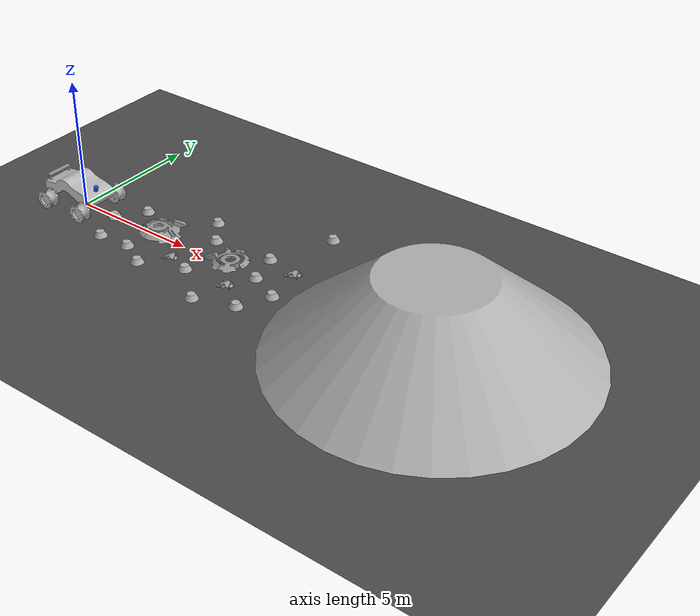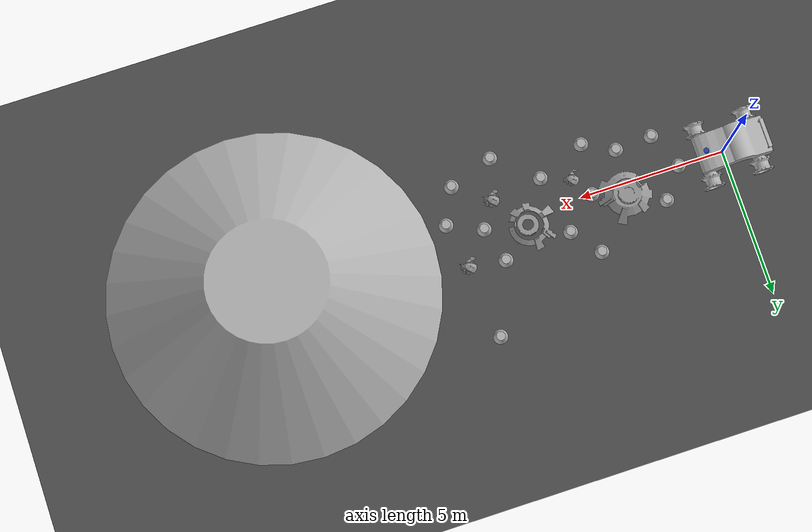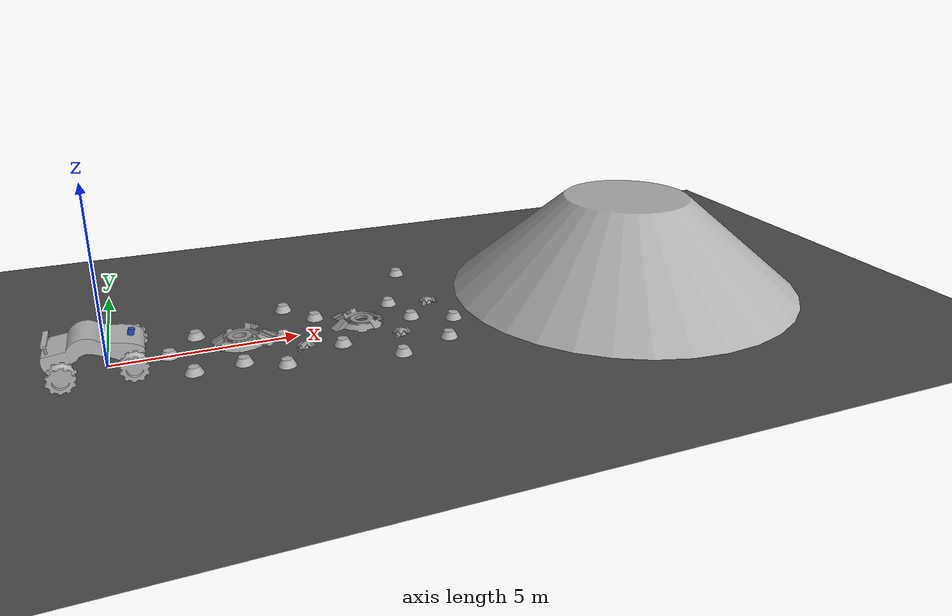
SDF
<sdf version="1.7">
 <world name="default">
  <light name="sun" type="directional">
   <pose>0 0 10 0 -0 0</pose>
   <diffuse>0.8 0.8 0.8 1</diffuse>
   <specular>0.2 0.2 0.2 1</specular>
   <attenuation>
    <range>1000</range>
    <constant>0.9</constant>
    <linear>0.01</linear>
    <quadratic>0.001</quadratic>
   </attenuation>
   <direction>-0.5 0.1 -0.9</direction>
   <spot><inner_angle>0</inner_angle><outer_angle>0</outer_angle><falloff>0</falloff></spot>
  </light>
  <model name="ground_plane">
   <static>1</static>
   <link name="link">
    <collision name="collision">
     <geometry><plane><normal>0 0 1</normal><size>100 100</size></plane></geometry>
     <surface><friction><ode><mu>100</mu><mu2>50</mu2></ode></friction></surface>
    </collision>
    <visual name="visual">
     <cast_shadows>0</cast_shadows>
     <geometry><plane><normal>0 0 1</normal><size>100 100</size></plane></geometry>
     <material>
      <script><uri>file://media/materials/scripts/gazebo.material</uri><name>Gazebo/DarkGrey</name></script>
     </material>
    </visual>
   </link>
  </model>
  <gravity>0 0 -1.62</gravity>
  <magnetic_field>6e-06 2.3e-05 -4.2e-05</magnetic_field>
  <atmosphere type="adiabatic"/>
  <physics type="ode">
   <max_step_size>0.001</max_step_size>
   <real_time_factor>1</real_time_factor>
   <real_time_update_rate>1000</real_time_update_rate>
  </physics>
  <scene><ambient>0.4 0.4 0.4 1</ambient><background>0.7 0.7 0.7 1</background><shadows>1</shadows></scene>
  <spherical_coordinates>
   <surface_model>EARTH_WGS84</surface_model>
   <latitude_deg>0</latitude_deg>
   <longitude_deg>0</longitude_deg>
   <elevation>0</elevation>
   <heading_deg>0</heading_deg>
  </spherical_coordinates>
  <model name="Mountain">
   <link name="link_0">
    <inertial>
     <mass>100</mass>
     <inertia><ixx>16.6667</ixx><ixy>0</ixy><ixz>0</ixz><iyy>16.6667</iyy><iyz>0</iyz><izz>16.6667</izz></inertia>
    </inertial>
    <kinematic>1</kinematic>
    <visual name="visual">
     <pose>0 0 1.5 0 -0 0</pose>
     <geometry>
      <mesh><uri>/home/user/ros2_ws/src/rover_5k/model/mountain/mountain.dae</uri><scale>1 1 1</scale></mesh>
     </geometry>
     <material>
      <lighting>1</lighting>
      <script>
       <uri>model://mountain/materials/scripts</uri>
       <uri>model://mountain/materials/textures</uri>
       <name>mountain</name>
      </script>
      <shader type="pixel"><normal_map>__default__</normal_map></shader>
      <ambient>0.3 0.3 0.3 1</ambient>
      <diffuse>0.7 0.7 0.7 1</diffuse>
      <specular>0.01 0.01 0.01 1</specular>
      <emissive>0 0 0 1</emissive>
     </material>
    </visual>
    <collision name="collision">
     <pose>0 0 1.5 0 -0 0</pose>
     <geometry>
      <mesh><uri>/home/user/ros2_ws/src/rover_5k/model/mountain/mountain.dae</uri><scale>1 1 1</scale></mesh>
     </geometry>
     <surface>
      <friction>
       <ode><mu>100</mu><mu2>50</mu2><fdir1>0 0 0</fdir1><slip1>0</slip1><slip2>0</slip2></ode>
       <torsional>
        <coefficient>1</coefficient>
        <patch_radius>0</patch_radius>
        <surface_radius>0</surface_radius>
        <use_patch_radius>1</use_patch_radius>
        <ode><slip>0</slip></ode>
       </torsional>
      </friction>
      <bounce><restitution_coefficient>0</restitution_coefficient><threshold>1e+06</threshold></bounce>
      <contact>
       <collide_without_contact>0</collide_without_contact>
       <collide_without_contact_bitmask>1</collide_without_contact_bitmask>
       <collide_bitmask>1</collide_bitmask>
       <ode>
        <soft_cfm>0</soft_cfm>
        <soft_erp>0.2</soft_erp>
        <kp>1e+13</kp>
        <kd>1</kd>
        <max_vel>0.01</max_vel>
        <min_depth>0</min_depth>
       </ode>
       <bullet>
        <split_impulse>1</split_impulse>
        <split_impulse_penetration_threshold>-0.01</split_impulse_penetration_threshold>
        <soft_cfm>0</soft_cfm>
        <soft_erp>0.2</soft_erp>
        <kp>1e+13</kp>
        <kd>1</kd>
       </bullet>
      </contact>
     </surface>
    </collision>
   </link>
   <static>0</static>
   <pose>15.6762 -0.009079 0 0 -0 0</pose>
  </model>
  <model name="block">
   <link name="link_0">
    <inertial>
     <mass>1</mass>
     <inertia>
      <ixx>0.166667</ixx>
      <ixy>0</ixy>
      <ixz>0</ixz>
      <iyy>0.166667</iyy>
      <iyz>0</iyz>
      <izz>0.166667</izz>
     </inertia>
    </inertial>
    <kinematic>1</kinematic>
    <visual name="visual">
     <pose>0 0 0.1 0 -0 0</pose>
     <geometry>
      <mesh><uri>/home/user/ros2_ws/src/rover_5k/model/block/block.dae</uri><scale>1 1 1</scale></mesh>
     </geometry>
     <material>
      <lighting>1</lighting>
      <script>
       <uri>model://block/materials/scripts</uri>
       <uri>model://block/materials/textures</uri>
       <name>block</name>
      </script>
      <shader type="pixel"><normal_map>__default__</normal_map></shader>
      <ambient>0.3 0.3 0.3 1</ambient>
      <diffuse>0.7 0.7 0.7 1</diffuse>
      <specular>0.01 0.01 0.01 1</specular>
      <emissive>0 0 0 1</emissive>
     </material>
    </visual>
    <collision name="collision">
     <pose>0 0 0.1 0 -0 0</pose>
     <geometry>
      <mesh><uri>/home/user/ros2_ws/src/rover_5k/model/block/block.dae</uri><scale>1 1 1</scale></mesh>
     </geometry>
     <surface>
      <friction>
       <ode><mu>1</mu><mu2>1</mu2><fdir1>0 0 0</fdir1><slip1>0</slip1><slip2>0</slip2></ode>
       <torsional>
        <coefficient>1</coefficient>
        <patch_radius>0</patch_radius>
        <surface_radius>0</surface_radius>
        <use_patch_radius>1</use_patch_radius>
        <ode><slip>0</slip></ode>
       </torsional>
      </friction>
      <bounce><restitution_coefficient>0</restitution_coefficient><threshold>1e+06</threshold></bounce>
      <contact>
       <collide_without_contact>0</collide_without_contact>
       <collide_without_contact_bitmask>1</collide_without_contact_bitmask>
       <collide_bitmask>1</collide_bitmask>
       <ode>
        <soft_cfm>0</soft_cfm>
        <soft_erp>0.2</soft_erp>
        <kp>1e+13</kp>
        <kd>1</kd>
        <max_vel>0.01</max_vel>
        <min_depth>0</min_depth>
       </ode>
       <bullet>
        <split_impulse>1</split_impulse>
        <split_impulse_penetration_threshold>-0.01</split_impulse_penetration_threshold>
        <soft_cfm>0</soft_cfm>
        <soft_erp>0.2</soft_erp>
        <kp>1e+13</kp>
        <kd>1</kd>
       </bullet>
      </contact>
     </surface>
    </collision>
   </link>
   <static>0</static>
   <pose>8.0258 1.2201 0 0 -0 0</pose>
  </model>
  <model name="block_0">
   <link name="link_0">
    <inertial>
     <mass>1</mass>
     <inertia>
      <ixx>0.166667</ixx>
      <ixy>0</ixy>
      <ixz>0</ixz>
      <iyy>0.166667</iyy>
      <iyz>0</iyz>
      <izz>0.166667</izz>
     </inertia>
    </inertial>
    <kinematic>1</kinematic>
    <visual name="visual">
     <pose>0 0 0.1 0 -0 0</pose>
     <geometry>
      <mesh><uri>/home/user/ros2_ws/src/rover_5k/model/block/block.dae</uri><scale>1 1 1</scale></mesh>
     </geometry>
     <material>
      <lighting>1</lighting>
      <script>
       <uri>model://block/materials/scripts</uri>
       <uri>model://block/materials/textures</uri>
       <name>block</name>
      </script>
      <shader type="pixel"><normal_map>__default__</normal_map></shader>
      <ambient>0.3 0.3 0.3 1</ambient>
      <diffuse>0.7 0.7 0.7 1</diffuse>
      <specular>0.01 0.01 0.01 1</specular>
      <emissive>0 0 0 1</emissive>
     </material>
    </visual>
    <collision name="collision">
     <pose>0 0 0.1 0 -0 0</pose>
     <geometry>
      <mesh><uri>/home/user/ros2_ws/src/rover_5k/model/block/block.dae</uri><scale>1 1 1</scale></mesh>
     </geometry>
     <surface>
      <friction>
       <ode><mu>1</mu><mu2>1</mu2><fdir1>0 0 0</fdir1><slip1>0</slip1><slip2>0</slip2></ode>
       <torsional>
        <coefficient>1</coefficient>
        <patch_radius>0</patch_radius>
        <surface_radius>0</surface_radius>
        <use_patch_radius>1</use_patch_radius>
        <ode><slip>0</slip></ode>
       </torsional>
      </friction>
      <bounce><restitution_coefficient>0</restitution_coefficient><threshold>1e+06</threshold></bounce>
      <contact>
       <collide_without_contact>0</collide_without_contact>
       <collide_without_contact_bitmask>1</collide_without_contact_bitmask>
       <collide_bitmask>1</collide_bitmask>
       <ode>
        <soft_cfm>0</soft_cfm>
        <soft_erp>0.2</soft_erp>
        <kp>1e+13</kp>
        <kd>1</kd>
        <max_vel>0.01</max_vel>
        <min_depth>0</min_depth>
       </ode>
       <bullet>
        <split_impulse>1</split_impulse>
        <split_impulse_penetration_threshold>-0.01</split_impulse_penetration_threshold>
        <soft_cfm>0</soft_cfm>
        <soft_erp>0.2</soft_erp>
        <kp>1e+13</kp>
        <kd>1</kd>
       </bullet>
      </contact>
     </surface>
    </collision>
   </link>
   <static>0</static>
   <pose>8.38174 0.010858 0 0 -0 0</pose>
  </model>
  <model name="block_1">
   <link name="link_0">
    <inertial>
     <mass>1</mass>
     <inertia>
      <ixx>0.166667</ixx>
      <ixy>0</ixy>
      <ixz>0</ixz>
      <iyy>0.166667</iyy>
      <iyz>0</iyz>
      <izz>0.166667</izz>
     </inertia>
    </inertial>
    <kinematic>1</kinematic>
    <visual name="visual">
     <pose>0 0 0.1 0 -0 0</pose>
     <geometry>
      <mesh><uri>/home/user/ros2_ws/src/rover_5k/model/block/block.dae</uri><scale>1 1 1</scale></mesh>
     </geometry>
     <material>
      <lighting>1</lighting>
      <script>
       <uri>model://block/materials/scripts</uri>
       <uri>model://block/materials/textures</uri>
       <name>block</name>
      </script>
      <shader type="pixel"><normal_map>__default__</normal_map></shader>
      <ambient>0.3 0.3 0.3 1</ambient>
      <diffuse>0.7 0.7 0.7 1</diffuse>
      <specular>0.01 0.01 0.01 1</specular>
      <emissive>0 0 0 1</emissive>
     </material>
    </visual>
    <collision name="collision">
     <pose>0 0 0.1 0 -0 0</pose>
     <geometry>
      <mesh><uri>/home/user/ros2_ws/src/rover_5k/model/block/block.dae</uri><scale>1 1 1</scale></mesh>
     </geometry>
     <surface>
      <friction>
       <ode><mu>1</mu><mu2>1</mu2><fdir1>0 0 0</fdir1><slip1>0</slip1><slip2>0</slip2></ode>
       <torsional>
        <coefficient>1</coefficient>
        <patch_radius>0</patch_radius>
        <surface_radius>0</surface_radius>
        <use_patch_radius>1</use_patch_radius>
        <ode><slip>0</slip></ode>
       </torsional>
      </friction>
      <bounce><restitution_coefficient>0</restitution_coefficient><threshold>1e+06</threshold></bounce>
      <contact>
       <collide_without_contact>0</collide_without_contact>
       <collide_without_contact_bitmask>1</collide_without_contact_bitmask>
       <collide_bitmask>1</collide_bitmask>
       <ode>
        <soft_cfm>0</soft_cfm>
        <soft_erp>0.2</soft_erp>
        <kp>1e+13</kp>
        <kd>1</kd>
        <max_vel>0.01</max_vel>
        <min_depth>0</min_depth>
       </ode>
       <bullet>
        <split_impulse>1</split_impulse>
        <split_impulse_penetration_threshold>-0.01</split_impulse_penetration_threshold>
        <soft_cfm>0</soft_cfm>
        <soft_erp>0.2</soft_erp>
        <kp>1e+13</kp>
        <kd>1</kd>
       </bullet>
      </contact>
     </surface>
    </collision>
   </link>
   <static>0</static>
   <pose>7.44651 -2.22069 0 0 -0 0</pose>
  </model>
  <model name="block_2">
   <link name="link_0">
    <inertial>
     <mass>1</mass>
     <inertia>
      <ixx>0.166667</ixx>
      <ixy>0</ixy>
      <ixz>0</ixz>
      <iyy>0.166667</iyy>
      <iyz>0</iyz>
      <izz>0.166667</izz>
     </inertia>
    </inertial>
    <kinematic>1</kinematic>
    <visual name="visual">
     <pose>0 0 0.1 0 -0 0</pose>
     <geometry>
      <mesh><uri>/home/user/ros2_ws/src/rover_5k/model/block/block.dae</uri><scale>1 1 1</scale></mesh>
     </geometry>
     <material>
      <lighting>1</lighting>
      <script>
       <uri>model://block/materials/scripts</uri>
       <uri>model://block/materials/textures</uri>
       <name>block</name>
      </script>
      <shader type="pixel"><normal_map>__default__</normal_map></shader>
      <ambient>0.3 0.3 0.3 1</ambient>
      <diffuse>0.7 0.7 0.7 1</diffuse>
      <specular>0.01 0.01 0.01 1</specular>
      <emissive>0 0 0 1</emissive>
     </material>
    </visual>
    <collision name="collision">
     <pose>0 0 0.1 0 -0 0</pose>
     <geometry>
      <mesh><uri>/home/user/ros2_ws/src/rover_5k/model/block/block.dae</uri><scale>1 1 1</scale></mesh>
     </geometry>
     <surface>
      <friction>
       <ode><mu>1</mu><mu2>1</mu2><fdir1>0 0 0</fdir1><slip1>0</slip1><slip2>0</slip2></ode>
       <torsional>
        <coefficient>1</coefficient>
        <patch_radius>0</patch_radius>
        <surface_radius>0</surface_radius>
        <use_patch_radius>1</use_patch_radius>
        <ode><slip>0</slip></ode>
       </torsional>
      </friction>
      <bounce><restitution_coefficient>0</restitution_coefficient><threshold>1e+06</threshold></bounce>
      <contact>
       <collide_without_contact>0</collide_without_contact>
       <collide_without_contact_bitmask>1</collide_without_contact_bitmask>
       <collide_bitmask>1</collide_bitmask>
       <ode>
        <soft_cfm>0</soft_cfm>
        <soft_erp>0.2</soft_erp>
        <kp>1e+13</kp>
        <kd>1</kd>
        <max_vel>0.01</max_vel>
        <min_depth>0</min_depth>
       </ode>
       <bullet>
        <split_impulse>1</split_impulse>
        <split_impulse_penetration_threshold>-0.01</split_impulse_penetration_threshold>
        <soft_cfm>0</soft_cfm>
        <soft_erp>0.2</soft_erp>
        <kp>1e+13</kp>
        <kd>1</kd>
       </bullet>
      </contact>
     </surface>
    </collision>
   </link>
   <static>0</static>
   <pose>4.92013 1.94206 0 0 -0 0</pose>
  </model>
  <model name="block_3">
   <link name="link_0">
    <inertial>
     <mass>1</mass>
     <inertia>
      <ixx>0.166667</ixx>
      <ixy>0</ixy>
      <ixz>0</ixz>
      <iyy>0.166667</iyy>
      <iyz>0</iyz>
      <izz>0.166667</izz>
     </inertia>
    </inertial>
    <kinematic>1</kinematic>
    <visual name="visual">
     <pose>0 0 0.1 0 -0 0</pose>
     <geometry>
      <mesh><uri>/home/user/ros2_ws/src/rover_5k/model/block/block.dae</uri><scale>1 1 1</scale></mesh>
     </geometry>
     <material>
      <lighting>1</lighting>
      <script>
       <uri>model://block/materials/scripts</uri>
       <uri>model://block/materials/textures</uri>
       <name>block</name>
      </script>
      <shader type="pixel"><normal_map>__default__</normal_map></shader>
      <ambient>0.3 0.3 0.3 1</ambient>
      <diffuse>0.7 0.7 0.7 1</diffuse>
      <specular>0.01 0.01 0.01 1</specular>
      <emissive>0 0 0 1</emissive>
     </material>
    </visual>
    <collision name="collision">
     <pose>0 0 0.1 0 -0 0</pose>
     <geometry>
      <mesh><uri>/home/user/ros2_ws/src/rover_5k/model/block/block.dae</uri><scale>1 1 1</scale></mesh>
     </geometry>
     <surface>
      <friction>
       <ode><mu>1</mu><mu2>1</mu2><fdir1>0 0 0</fdir1><slip1>0</slip1><slip2>0</slip2></ode>
       <torsional>
        <coefficient>1</coefficient>
        <patch_radius>0</patch_radius>
        <surface_radius>0</surface_radius>
        <use_patch_radius>1</use_patch_radius>
        <ode><slip>0</slip></ode>
       </torsional>
      </friction>
      <bounce><restitution_coefficient>0</restitution_coefficient><threshold>1e+06</threshold></bounce>
      <contact>
       <collide_without_contact>0</collide_without_contact>
       <collide_without_contact_bitmask>1</collide_without_contact_bitmask>
       <collide_bitmask>1</collide_bitmask>
       <ode>
        <soft_cfm>0</soft_cfm>
        <soft_erp>0.2</soft_erp>
        <kp>1e+13</kp>
        <kd>1</kd>
        <max_vel>0.01</max_vel>
        <min_depth>0</min_depth>
       </ode>
       <bullet>
        <split_impulse>1</split_impulse>
        <split_impulse_penetration_threshold>-0.01</split_impulse_penetration_threshold>
        <soft_cfm>0</soft_cfm>
        <soft_erp>0.2</soft_erp>
        <kp>1e+13</kp>
        <kd>1</kd>
       </bullet>
      </contact>
     </surface>
    </collision>
   </link>
   <static>0</static>
   <pose>9.00225 3.58967 0 0 -0 0</pose>
  </model>
  <model name="block_4">
   <link name="link_0">
    <inertial>
     <mass>1</mass>
     <inertia>
      <ixx>0.166667</ixx>
      <ixy>0</ixy>
      <ixz>0</ixz>
      <iyy>0.166667</iyy>
      <iyz>0</iyz>
      <izz>0.166667</izz>
     </inertia>
    </inertial>
    <kinematic>1</kinematic>
    <visual name="visual">
     <pose>0 0 0.1 0 -0 0</pose>
     <geometry>
      <mesh><uri>/home/user/ros2_ws/src/rover_5k/model/block/block.dae</uri><scale>1 1 1</scale></mesh>
     </geometry>
     <material>
      <lighting>1</lighting>
      <script>
       <uri>model://block/materials/scripts</uri>
       <uri>model://block/materials/textures</uri>
       <name>block</name>
      </script>
      <shader type="pixel"><normal_map>__default__</normal_map></shader>
      <ambient>0.3 0.3 0.3 1</ambient>
      <diffuse>0.7 0.7 0.7 1</diffuse>
      <specular>0.01 0.01 0.01 1</specular>
      <emissive>0 0 0 1</emissive>
     </material>
    </visual>
    <collision name="collision">
     <pose>0 0 0.1 0 -0 0</pose>
     <geometry>
      <mesh><uri>/home/user/ros2_ws/src/rover_5k/model/block/block.dae</uri><scale>1 1 1</scale></mesh>
     </geometry>
     <surface>
      <friction>
       <ode><mu>1</mu><mu2>1</mu2><fdir1>0 0 0</fdir1><slip1>0</slip1><slip2>0</slip2></ode>
       <torsional>
        <coefficient>1</coefficient>
        <patch_radius>0</patch_radius>
        <surface_radius>0</surface_radius>
        <use_patch_radius>1</use_patch_radius>
        <ode><slip>0</slip></ode>
       </torsional>
      </friction>
      <bounce><restitution_coefficient>0</restitution_coefficient><threshold>1e+06</threshold></bounce>
      <contact>
       <collide_without_contact>0</collide_without_contact>
       <collide_without_contact_bitmask>1</collide_without_contact_bitmask>
       <collide_bitmask>1</collide_bitmask>
       <ode>
        <soft_cfm>0</soft_cfm>
        <soft_erp>0.2</soft_erp>
        <kp>1e+13</kp>
        <kd>1</kd>
        <max_vel>0.01</max_vel>
        <min_depth>0</min_depth>
       </ode>
       <bullet>
        <split_impulse>1</split_impulse>
        <split_impulse_penetration_threshold>-0.01</split_impulse_penetration_threshold>
        <soft_cfm>0</soft_cfm>
        <soft_erp>0.2</soft_erp>
        <kp>1e+13</kp>
        <kd>1</kd>
       </bullet>
      </contact>
     </surface>
    </collision>
   </link>
   <static>0</static>
   <pose>4.39891 -1.73265 0 0 -0 0</pose>
  </model>
  <model name="block_5">
   <link name="link_0">
    <inertial>
     <mass>1</mass>
     <inertia>
      <ixx>0.166667</ixx>
      <ixy>0</ixy>
      <ixz>0</ixz>
      <iyy>0.166667</iyy>
      <iyz>0</iyz>
      <izz>0.166667</izz>
     </inertia>
    </inertial>
    <kinematic>1</kinematic>
    <visual name="visual">
     <pose>0 0 0.1 0 -0 0</pose>
     <geometry>
      <mesh><uri>/home/user/ros2_ws/src/rover_5k/model/block/block.dae</uri><scale>1 1 1</scale></mesh>
     </geometry>
     <material>
      <lighting>1</lighting>
      <script>
       <uri>model://block/materials/scripts</uri>
       <uri>model://block/materials/textures</uri>
       <name>block</name>
      </script>
      <shader type="pixel"><normal_map>__default__</normal_map></shader>
      <ambient>0.3 0.3 0.3 1</ambient>
      <diffuse>0.7 0.7 0.7 1</diffuse>
      <specular>0.01 0.01 0.01 1</specular>
      <emissive>0 0 0 1</emissive>
     </material>
    </visual>
    <collision name="collision">
     <pose>0 0 0.1 0 -0 0</pose>
     <geometry>
      <mesh><uri>/home/user/ros2_ws/src/rover_5k/model/block/block.dae</uri><scale>1 1 1</scale></mesh>
     </geometry>
     <surface>
      <friction>
       <ode><mu>1</mu><mu2>1</mu2><fdir1>0 0 0</fdir1><slip1>0</slip1><slip2>0</slip2></ode>
       <torsional>
        <coefficient>1</coefficient>
        <patch_radius>0</patch_radius>
        <surface_radius>0</surface_radius>
        <use_patch_radius>1</use_patch_radius>
        <ode><slip>0</slip></ode>
       </torsional>
      </friction>
      <bounce><restitution_coefficient>0</restitution_coefficient><threshold>1e+06</threshold></bounce>
      <contact>
       <collide_without_contact>0</collide_without_contact>
       <collide_without_contact_bitmask>1</collide_without_contact_bitmask>
       <collide_bitmask>1</collide_bitmask>
       <ode>
        <soft_cfm>0</soft_cfm>
        <soft_erp>0.2</soft_erp>
        <kp>1e+13</kp>
        <kd>1</kd>
        <max_vel>0.01</max_vel>
        <min_depth>0</min_depth>
       </ode>
       <bullet>
        <split_impulse>1</split_impulse>
        <split_impulse_penetration_threshold>-0.01</split_impulse_penetration_threshold>
        <soft_cfm>0</soft_cfm>
        <soft_erp>0.2</soft_erp>
        <kp>1e+13</kp>
        <kd>1</kd>
       </bullet>
      </contact>
     </surface>
    </collision>
   </link>
   <static>0</static>
   <pose>4.59787 -0.002678 0 0 -0 0</pose>
  </model>
  <model name="block_6">
   <link name="link_0">
    <inertial>
     <mass>1</mass>
     <inertia>
      <ixx>0.166667</ixx>
      <ixy>0</ixy>
      <ixz>0</ixz>
      <iyy>0.166667</iyy>
      <iyz>0</iyz>
      <izz>0.166667</izz>
     </inertia>
    </inertial>
    <kinematic>1</kinematic>
    <visual name="visual">
     <pose>0 0 0.1 0 -0 0</pose>
     <geometry>
      <mesh><uri>/home/user/ros2_ws/src/rover_5k/model/block/block.dae</uri><scale>1 1 1</scale></mesh>
     </geometry>
     <material>
      <lighting>1</lighting>
      <script>
       <uri>model://block/materials/scripts</uri>
       <uri>model://block/materials/textures</uri>
       <name>block</name>
      </script>
      <shader type="pixel"><normal_map>__default__</normal_map></shader>
      <ambient>0.3 0.3 0.3 1</ambient>
      <diffuse>0.7 0.7 0.7 1</diffuse>
      <specular>0.01 0.01 0.01 1</specular>
      <emissive>0 0 0 1</emissive>
     </material>
    </visual>
    <collision name="collision">
     <pose>0 0 0.1 0 -0 0</pose>
     <geometry>
      <mesh><uri>/home/user/ros2_ws/src/rover_5k/model/block/block.dae</uri><scale>1 1 1</scale></mesh>
     </geometry>
     <surface>
      <friction>
       <ode><mu>1</mu><mu2>1</mu2><fdir1>0 0 0</fdir1><slip1>0</slip1><slip2>0</slip2></ode>
       <torsional>
        <coefficient>1</coefficient>
        <patch_radius>0</patch_radius>
        <surface_radius>0</surface_radius>
        <use_patch_radius>1</use_patch_radius>
        <ode><slip>0</slip></ode>
       </torsional>
      </friction>
      <bounce><restitution_coefficient>0</restitution_coefficient><threshold>1e+06</threshold></bounce>
      <contact>
       <collide_without_contact>0</collide_without_contact>
       <collide_without_contact_bitmask>1</collide_without_contact_bitmask>
       <collide_bitmask>1</collide_bitmask>
       <ode>
        <soft_cfm>0</soft_cfm>
        <soft_erp>0.2</soft_erp>
        <kp>1e+13</kp>
        <kd>1</kd>
        <max_vel>0.01</max_vel>
        <min_depth>0</min_depth>
       </ode>
       <bullet>
        <split_impulse>1</split_impulse>
        <split_impulse_penetration_threshold>-0.01</split_impulse_penetration_threshold>
        <soft_cfm>0</soft_cfm>
        <soft_erp>0.2</soft_erp>
        <kp>1e+13</kp>
        <kd>1</kd>
       </bullet>
      </contact>
     </surface>
    </collision>
   </link>
   <static>0</static>
   <pose>5.68725 0.982847 0 0 -0 0</pose>
  </model>
  <model name="block_7">
   <link name="link_0">
    <inertial>
     <mass>1</mass>
     <inertia>
      <ixx>0.166667</ixx>
      <ixy>0</ixy>
      <ixz>0</ixz>
      <iyy>0.166667</iyy>
      <iyz>0</iyz>
      <izz>0.166667</izz>
     </inertia>
    </inertial>
    <kinematic>1</kinematic>
    <visual name="visual">
     <pose>0 0 0.1 0 -0 0</pose>
     <geometry>
      <mesh><uri>/home/user/ros2_ws/src/rover_5k/model/block/block.dae</uri><scale>1 1 1</scale></mesh>
     </geometry>
     <material>
      <lighting>1</lighting>
      <script>
       <uri>model://block/materials/scripts</uri>
       <uri>model://block/materials/textures</uri>
       <name>block</name>
      </script>
      <shader type="pixel"><normal_map>__default__</normal_map></shader>
      <ambient>0.3 0.3 0.3 1</ambient>
      <diffuse>0.7 0.7 0.7 1</diffuse>
      <specular>0.01 0.01 0.01 1</specular>
      <emissive>0 0 0 1</emissive>
     </material>
    </visual>
    <collision name="collision">
     <pose>0 0 0.1 0 -0 0</pose>
     <geometry>
      <mesh><uri>/home/user/ros2_ws/src/rover_5k/model/block/block.dae</uri><scale>1 1 1</scale></mesh>
     </geometry>
     <surface>
      <friction>
       <ode><mu>1</mu><mu2>1</mu2><fdir1>0 0 0</fdir1><slip1>0</slip1><slip2>0</slip2></ode>
       <torsional>
        <coefficient>1</coefficient>
        <patch_radius>0</patch_radius>
        <surface_radius>0</surface_radius>
        <use_patch_radius>1</use_patch_radius>
        <ode><slip>0</slip></ode>
       </torsional>
      </friction>
      <bounce><restitution_coefficient>0</restitution_coefficient><threshold>1e+06</threshold></bounce>
      <contact>
       <collide_without_contact>0</collide_without_contact>
       <collide_without_contact_bitmask>1</collide_without_contact_bitmask>
       <collide_bitmask>1</collide_bitmask>
       <ode>
        <soft_cfm>0</soft_cfm>
        <soft_erp>0.2</soft_erp>
        <kp>1e+13</kp>
        <kd>1</kd>
        <max_vel>0.01</max_vel>
        <min_depth>0</min_depth>
       </ode>
       <bullet>
        <split_impulse>1</split_impulse>
        <split_impulse_penetration_threshold>-0.01</split_impulse_penetration_threshold>
        <soft_cfm>0</soft_cfm>
        <soft_erp>0.2</soft_erp>
        <kp>1e+13</kp>
        <kd>1</kd>
       </bullet>
      </contact>
     </surface>
    </collision>
   </link>
   <static>0</static>
   <pose>2.08393 -1.27182 0 0 -0 0</pose>
  </model>
  <model name="block_8">
   <link name="link_0">
    <inertial>
     <mass>1</mass>
     <inertia>
      <ixx>0.166667</ixx>
      <ixy>0</ixy>
      <ixz>0</ixz>
      <iyy>0.166667</iyy>
      <iyz>0</iyz>
      <izz>0.166667</izz>
     </inertia>
    </inertial>
    <kinematic>1</kinematic>
    <visual name="visual">
     <pose>0 0 0.1 0 -0 0</pose>
     <geometry>
      <mesh><uri>/home/user/ros2_ws/src/rover_5k/model/block/block.dae</uri><scale>1 1 1</scale></mesh>
     </geometry>
     <material>
      <lighting>1</lighting>
      <script>
       <uri>model://block/materials/scripts</uri>
       <uri>model://block/materials/textures</uri>
       <name>block</name>
      </script>
      <shader type="pixel"><normal_map>__default__</normal_map></shader>
      <ambient>0.3 0.3 0.3 1</ambient>
      <diffuse>0.7 0.7 0.7 1</diffuse>
      <specular>0.01 0.01 0.01 1</specular>
      <emissive>0 0 0 1</emissive>
     </material>
    </visual>
    <collision name="collision">
     <pose>0 0 0.1 0 -0 0</pose>
     <geometry>
      <mesh><uri>/home/user/ros2_ws/src/rover_5k/model/block/block.dae</uri><scale>1 1 1</scale></mesh>
     </geometry>
     <surface>
      <friction>
       <ode><mu>1</mu><mu2>1</mu2><fdir1>0 0 0</fdir1><slip1>0</slip1><slip2>0</slip2></ode>
       <torsional>
        <coefficient>1</coefficient>
        <patch_radius>0</patch_radius>
        <surface_radius>0</surface_radius>
        <use_patch_radius>1</use_patch_radius>
        <ode><slip>0</slip></ode>
       </torsional>
      </friction>
      <bounce><restitution_coefficient>0</restitution_coefficient><threshold>1e+06</threshold></bounce>
      <contact>
       <collide_without_contact>0</collide_without_contact>
       <collide_without_contact_bitmask>1</collide_without_contact_bitmask>
       <collide_bitmask>1</collide_bitmask>
       <ode>
        <soft_cfm>0</soft_cfm>
        <soft_erp>0.2</soft_erp>
        <kp>1e+13</kp>
        <kd>1</kd>
        <max_vel>0.01</max_vel>
        <min_depth>0</min_depth>
       </ode>
       <bullet>
        <split_impulse>1</split_impulse>
        <split_impulse_penetration_threshold>-0.01</split_impulse_penetration_threshold>
        <soft_cfm>0</soft_cfm>
        <soft_erp>0.2</soft_erp>
        <kp>1e+13</kp>
        <kd>1</kd>
       </bullet>
      </contact>
     </surface>
    </collision>
   </link>
   <static>0</static>
   <pose>2.29947 0.958075 0 0 -0 0</pose>
  </model>
  <model name="block_9">
   <link name="link_0">
    <inertial>
     <mass>1</mass>
     <inertia>
      <ixx>0.166667</ixx>
      <ixy>0</ixy>
      <ixz>0</ixz>
      <iyy>0.166667</iyy>
      <iyz>0</iyz>
      <izz>0.166667</izz>
     </inertia>
    </inertial>
    <kinematic>1</kinematic>
    <visual name="visual">
     <pose>0 0 0.1 0 -0 0</pose>
     <geometry>
      <mesh><uri>/home/user/ros2_ws/src/rover_5k/model/block/block.dae</uri><scale>1 1 1</scale></mesh>
     </geometry>
     <material>
      <lighting>1</lighting>
      <script>
       <uri>model://block/materials/scripts</uri>
       <uri>model://block/materials/textures</uri>
       <name>block</name>
      </script>
      <shader type="pixel"><normal_map>__default__</normal_map></shader>
      <ambient>0.3 0.3 0.3 1</ambient>
      <diffuse>0.7 0.7 0.7 1</diffuse>
      <specular>0.01 0.01 0.01 1</specular>
      <emissive>0 0 0 1</emissive>
     </material>
    </visual>
    <collision name="collision">
     <pose>0 0 0.1 0 -0 0</pose>
     <geometry>
      <mesh><uri>/home/user/ros2_ws/src/rover_5k/model/block/block.dae</uri><scale>1 1 1</scale></mesh>
     </geometry>
     <surface>
      <friction>
       <ode><mu>1</mu><mu2>1</mu2><fdir1>0 0 0</fdir1><slip1>0</slip1><slip2>0</slip2></ode>
       <torsional>
        <coefficient>1</coefficient>
        <patch_radius>0</patch_radius>
        <surface_radius>0</surface_radius>
        <use_patch_radius>1</use_patch_radius>
        <ode><slip>0</slip></ode>
       </torsional>
      </friction>
      <bounce><restitution_coefficient>0</restitution_coefficient><threshold>1e+06</threshold></bounce>
      <contact>
       <collide_without_contact>0</collide_without_contact>
       <collide_without_contact_bitmask>1</collide_without_contact_bitmask>
       <collide_bitmask>1</collide_bitmask>
       <ode>
        <soft_cfm>0</soft_cfm>
        <soft_erp>0.2</soft_erp>
        <kp>1e+13</kp>
        <kd>1</kd>
        <max_vel>0.01</max_vel>
        <min_depth>0</min_depth>
       </ode>
       <bullet>
        <split_impulse>1</split_impulse>
        <split_impulse_penetration_threshold>-0.01</split_impulse_penetration_threshold>
        <soft_cfm>0</soft_cfm>
        <soft_erp>0.2</soft_erp>
        <kp>1e+13</kp>
        <kd>1</kd>
       </bullet>
      </contact>
     </surface>
    </collision>
   </link>
   <static>0</static>
   <pose>6.05444 -1.05533 0 0 -0 0</pose>
  </model>
  <model name="block_10">
   <link name="link_0">
    <inertial>
     <mass>1</mass>
     <inertia>
      <ixx>0.166667</ixx>
      <ixy>0</ixy>
      <ixz>0</ixz>
      <iyy>0.166667</iyy>
      <iyz>0</iyz>
      <izz>0.166667</izz>
     </inertia>
    </inertial>
    <kinematic>1</kinematic>
    <visual name="visual">
     <pose>0 0 0.1 0 -0 0</pose>
     <geometry>
      <mesh><uri>/home/user/ros2_ws/src/rover_5k/model/block/block.dae</uri><scale>1 1 1</scale></mesh>
     </geometry>
     <material>
      <lighting>1</lighting>
      <script>
       <uri>model://block/materials/scripts</uri>
       <uri>model://block/materials/textures</uri>
       <name>block</name>
      </script>
      <shader type="pixel"><normal_map>__default__</normal_map></shader>
      <ambient>0.3 0.3 0.3 1</ambient>
      <diffuse>0.7 0.7 0.7 1</diffuse>
      <specular>0.01 0.01 0.01 1</specular>
      <emissive>0 0 0 1</emissive>
     </material>
    </visual>
    <collision name="collision">
     <pose>0 0 0.1 0 -0 0</pose>
     <geometry>
      <mesh><uri>/home/user/ros2_ws/src/rover_5k/model/block/block.dae</uri><scale>1 1 1</scale></mesh>
     </geometry>
     <surface>
      <friction>
       <ode><mu>1</mu><mu2>1</mu2><fdir1>0 0 0</fdir1><slip1>0</slip1><slip2>0</slip2></ode>
       <torsional>
        <coefficient>1</coefficient>
        <patch_radius>0</patch_radius>
        <surface_radius>0</surface_radius>
        <use_patch_radius>1</use_patch_radius>
        <ode><slip>0</slip></ode>
       </torsional>
      </friction>
      <bounce><restitution_coefficient>0</restitution_coefficient><threshold>1e+06</threshold></bounce>
      <contact>
       <collide_without_contact>0</collide_without_contact>
       <collide_without_contact_bitmask>1</collide_without_contact_bitmask>
       <collide_bitmask>1</collide_bitmask>
       <ode>
        <soft_cfm>0</soft_cfm>
        <soft_erp>0.2</soft_erp>
        <kp>1e+13</kp>
        <kd>1</kd>
        <max_vel>0.01</max_vel>
        <min_depth>0</min_depth>
       </ode>
       <bullet>
        <split_impulse>1</split_impulse>
        <split_impulse_penetration_threshold>-0.01</split_impulse_penetration_threshold>
        <soft_cfm>0</soft_cfm>
        <soft_erp>0.2</soft_erp>
        <kp>1e+13</kp>
        <kd>1</kd>
       </bullet>
      </contact>
     </surface>
    </collision>
   </link>
   <static>0</static>
   <pose>3.35846 -1.19015 0 0 -0 0</pose>
  </model>
  <model name="block_11">
   <link name="link_0">
    <inertial>
     <mass>1</mass>
     <inertia>
      <ixx>0.166667</ixx>
      <ixy>0</ixy>
      <ixz>0</ixz>
      <iyy>0.166667</iyy>
      <iyz>0</iyz>
      <izz>0.166667</izz>
     </inertia>
    </inertial>
    <kinematic>1</kinematic>
    <visual name="visual">
     <pose>0 0 0.1 0 -0 0</pose>
     <geometry>
      <mesh><uri>/home/user/ros2_ws/src/rover_5k/model/block/block.dae</uri><scale>1 1 1</scale></mesh>
     </geometry>
     <material>
      <lighting>1</lighting>
      <script>
       <uri>model://block/materials/scripts</uri>
       <uri>model://block/materials/textures</uri>
       <name>block</name>
      </script>
      <shader type="pixel"><normal_map>__default__</normal_map></shader>
      <ambient>0.3 0.3 0.3 1</ambient>
      <diffuse>0.7 0.7 0.7 1</diffuse>
      <specular>0.01 0.01 0.01 1</specular>
      <emissive>0 0 0 1</emissive>
     </material>
    </visual>
    <collision name="collision">
     <pose>0 0 0.1 0 -0 0</pose>
     <geometry>
      <mesh><uri>/home/user/ros2_ws/src/rover_5k/model/block/block.dae</uri><scale>1 1 1</scale></mesh>
     </geometry>
     <surface>
      <friction>
       <ode><mu>1</mu><mu2>1</mu2><fdir1>0 0 0</fdir1><slip1>0</slip1><slip2>0</slip2></ode>
       <torsional>
        <coefficient>1</coefficient>
        <patch_radius>0</patch_radius>
        <surface_radius>0</surface_radius>
        <use_patch_radius>1</use_patch_radius>
        <ode><slip>0</slip></ode>
       </torsional>
      </friction>
      <bounce><restitution_coefficient>0</restitution_coefficient><threshold>1e+06</threshold></bounce>
      <contact>
       <collide_without_contact>0</collide_without_contact>
       <collide_without_contact_bitmask>1</collide_without_contact_bitmask>
       <collide_bitmask>1</collide_bitmask>
       <ode>
        <soft_cfm>0</soft_cfm>
        <soft_erp>0.2</soft_erp>
        <kp>1e+13</kp>
        <kd>1</kd>
        <max_vel>0.01</max_vel>
        <min_depth>0</min_depth>
       </ode>
       <bullet>
        <split_impulse>1</split_impulse>
        <split_impulse_penetration_threshold>-0.01</split_impulse_penetration_threshold>
        <soft_cfm>0</soft_cfm>
        <soft_erp>0.2</soft_erp>
        <kp>1e+13</kp>
        <kd>1</kd>
       </bullet>
      </contact>
     </surface>
    </collision>
   </link>
   <static>0</static>
   <pose>1.5402 -0.030778 0 0 -0 0</pose>
  </model>
  <model name="block2">
   <link name="link_0">
    <inertial>
     <mass>10</mass>
     <inertia>
      <ixx>0.166667</ixx>
      <ixy>0</ixy>
      <ixz>0</ixz>
      <iyy>0.166667</iyy>
      <iyz>0</iyz>
      <izz>0.166667</izz>
     </inertia>
    </inertial>
    <kinematic>1</kinematic>
    <visual name="visual">
     <geometry>
      <mesh><uri>/home/user/ros2_ws/src/rover_5k/model/block2/block2.dae</uri><scale>1 1 1</scale></mesh>
     </geometry>
     <material>
      <lighting>1</lighting>
      <script><uri>file://media/materials/scripts/gazebo.material</uri><name>Gazebo/Grey</name></script>
      <shader type="pixel"><normal_map>__default__</normal_map></shader>
      <ambient>0.3 0.3 0.3 1</ambient>
      <diffuse>0.7 0.7 0.7 1</diffuse>
      <specular>0.01 0.01 0.01 1</specular>
      <emissive>0 0 0 1</emissive>
     </material>
    </visual>
    <collision name="collision">
     <geometry>
      <mesh><uri>/home/user/ros2_ws/src/rover_5k/model/block2/block2.dae</uri><scale>1 1 1</scale></mesh>
     </geometry>
     <surface>
      <friction>
       <ode><mu>1</mu><mu2>1</mu2><fdir1>0 0 0</fdir1><slip1>0</slip1><slip2>0</slip2></ode>
       <torsional>
        <coefficient>1</coefficient>
        <patch_radius>0</patch_radius>
        <surface_radius>0</surface_radius>
        <use_patch_radius>1</use_patch_radius>
        <ode><slip>0</slip></ode>
       </torsional>
      </friction>
      <bounce><restitution_coefficient>0</restitution_coefficient><threshold>1e+06</threshold></bounce>
      <contact>
       <collide_without_contact>0</collide_without_contact>
       <collide_without_contact_bitmask>1</collide_without_contact_bitmask>
       <collide_bitmask>1</collide_bitmask>
       <ode>
        <soft_cfm>0</soft_cfm>
        <soft_erp>0.2</soft_erp>
        <kp>1e+13</kp>
        <kd>1</kd>
        <max_vel>0.01</max_vel>
        <min_depth>0</min_depth>
       </ode>
       <bullet>
        <split_impulse>1</split_impulse>
        <split_impulse_penetration_threshold>-0.01</split_impulse_penetration_threshold>
        <soft_cfm>0</soft_cfm>
        <soft_erp>0.2</soft_erp>
        <kp>1e+13</kp>
        <kd>1</kd>
       </bullet>
      </contact>
     </surface>
    </collision>
   </link>
   <static>0</static>
   <pose>3.47551 0.340274 -0.019946 0 0 -2.40443</pose>
  </model>
  <model name="block3">
   <link name="link_1">
    <inertial>
     <mass>10</mass>
     <inertia>
      <ixx>0.166667</ixx>
      <ixy>0</ixy>
      <ixz>0</ixz>
      <iyy>0.166667</iyy>
      <iyz>0</iyz>
      <izz>0.166667</izz>
     </inertia>
    </inertial>
    <kinematic>1</kinematic>
    <visual name="visual">
     <geometry>
      <mesh><uri>/home/user/ros2_ws/src/rover_5k/model/block3/block3.dae</uri><scale>1 1 1</scale></mesh>
     </geometry>
     <material>
      <lighting>1</lighting>
      <script><uri>file://media/materials/scripts/gazebo.material</uri><name>Gazebo/Grey</name></script>
      <shader type="pixel"><normal_map>__default__</normal_map></shader>
      <ambient>0.3 0.3 0.3 1</ambient>
      <diffuse>0.7 0.7 0.7 1</diffuse>
      <specular>0.01 0.01 0.01 1</specular>
      <emissive>0 0 0 1</emissive>
     </material>
    </visual>
    <collision name="collision">
     <geometry>
      <mesh><uri>/home/user/ros2_ws/src/rover_5k/model/block3/block3.dae</uri><scale>1 1 1</scale></mesh>
     </geometry>
     <surface>
      <friction>
       <ode><mu>1</mu><mu2>1</mu2><fdir1>0 0 0</fdir1><slip1>0</slip1><slip2>0</slip2></ode>
       <torsional>
        <coefficient>1</coefficient>
        <patch_radius>0</patch_radius>
        <surface_radius>0</surface_radius>
        <use_patch_radius>1</use_patch_radius>
        <ode><slip>0</slip></ode>
       </torsional>
      </friction>
      <bounce><restitution_coefficient>0</restitution_coefficient><threshold>1e+06</threshold></bounce>
      <contact>
       <collide_without_contact>0</collide_without_contact>
       <collide_without_contact_bitmask>1</collide_without_contact_bitmask>
       <collide_bitmask>1</collide_bitmask>
       <ode>
        <soft_cfm>0</soft_cfm>
        <soft_erp>0.2</soft_erp>
        <kp>1e+13</kp>
        <kd>1</kd>
        <max_vel>0.01</max_vel>
        <min_depth>0</min_depth>
       </ode>
       <bullet>
        <split_impulse>1</split_impulse>
        <split_impulse_penetration_threshold>-0.01</split_impulse_penetration_threshold>
        <soft_cfm>0</soft_cfm>
        <soft_erp>0.2</soft_erp>
        <kp>1e+13</kp>
        <kd>1</kd>
       </bullet>
      </contact>
     </surface>
    </collision>
   </link>
   <static>0</static>
   <pose>5.05908 -0.680988 -0.190044 0 -0 0</pose>
  </model>
  <model name="block3_1">
   <link name="link_1">
    <inertial>
     <mass>10</mass>
     <inertia>
      <ixx>0.166667</ixx>
      <ixy>0</ixy>
      <ixz>0</ixz>
      <iyy>0.166667</iyy>
      <iyz>0</iyz>
      <izz>0.166667</izz>
     </inertia>
    </inertial>
    <kinematic>1</kinematic>
    <visual name="visual">
     <geometry>
      <mesh><uri>/home/user/ros2_ws/src/rover_5k/model/block3/block3.dae</uri><scale>1 1 1</scale></mesh>
     </geometry>
     <material>
      <lighting>1</lighting>
      <script><uri>file://media/materials/scripts/gazebo.material</uri><name>Gazebo/Grey</name></script>
      <shader type="pixel"><normal_map>__default__</normal_map></shader>
      <ambient>0.3 0.3 0.3 1</ambient>
      <diffuse>0.7 0.7 0.7 1</diffuse>
      <specular>0.01 0.01 0.01 1</specular>
      <emissive>0 0 0 1</emissive>
     </material>
    </visual>
    <collision name="collision">
     <geometry>
      <mesh><uri>/home/user/ros2_ws/src/rover_5k/model/block3/block3.dae</uri><scale>1 1 1</scale></mesh>
     </geometry>
     <surface>
      <friction>
       <ode><mu>1</mu><mu2>1</mu2><fdir1>0 0 0</fdir1><slip1>0</slip1><slip2>0</slip2></ode>
       <torsional>
        <coefficient>1</coefficient>
        <patch_radius>0</patch_radius>
        <surface_radius>0</surface_radius>
        <use_patch_radius>1</use_patch_radius>
        <ode><slip>0</slip></ode>
       </torsional>
      </friction>
      <bounce><restitution_coefficient>0</restitution_coefficient><threshold>1e+06</threshold></bounce>
      <contact>
       <collide_without_contact>0</collide_without_contact>
       <collide_without_contact_bitmask>1</collide_without_contact_bitmask>
       <collide_bitmask>1</collide_bitmask>
       <ode>
        <soft_cfm>0</soft_cfm>
        <soft_erp>0.2</soft_erp>
        <kp>1e+13</kp>
        <kd>1</kd>
        <max_vel>0.01</max_vel>
        <min_depth>0</min_depth>
       </ode>
       <bullet>
        <split_impulse>1</split_impulse>
        <split_impulse_penetration_threshold>-0.01</split_impulse_penetration_threshold>
        <soft_cfm>0</soft_cfm>
        <soft_erp>0.2</soft_erp>
        <kp>1e+13</kp>
        <kd>1</kd>
       </bullet>
      </contact>
     </surface>
    </collision>
   </link>
   <static>0</static>
   <pose>9.23682 1.06527 -0.167805 0 -0 0</pose>
  </model>
  <model name="rover_5k">
   <link name="Body">
    <inertial>
     <mass>20</mass>
     <inertia><ixx>3.22227</ixx><ixy>0</ixy><ixz>0</ixz><iyy>3.22227</iyy><iyz>0</iyz><izz>3.22227</izz></inertia>
    </inertial>
    <pose>0 0 0.5 0 -0 0</pose>
    <visual name="visual">
     <pose>0 0 -0.7 0 0 -1.5707</pose>
     <geometry>
      <mesh><uri>/home/user/ros2_ws/src/rover_5k/model/rover/dae/body.dae</uri><scale>0.5 0.5 0.5</scale></mesh>
     </geometry>
     <material>
      <script>
       <uri>model://rover/materials/scripts</uri>
       <uri>model://rover/materials/textures</uri>
       <name>rover/surface</name>
      </script>
     </material>
    </visual>
    <collision name="collision">
     <pose>0 0 -0.7 0 0 -1.5707</pose>
     <geometry>
      <mesh><uri>/home/user/ros2_ws/src/rover_5k/model/rover/dae/body.dae</uri><scale>0.5 0.5 0.5</scale></mesh>
     </geometry>
     <surface>
      <friction>
       <ode><mu>1</mu><mu2>1</mu2><fdir1>0 0 0</fdir1><slip1>0</slip1><slip2>0</slip2></ode>
       <torsional>
        <coefficient>1</coefficient>
        <patch_radius>0</patch_radius>
        <surface_radius>0</surface_radius>
        <use_patch_radius>1</use_patch_radius>
        <ode><slip>0</slip></ode>
       </torsional>
      </friction>
      <bounce><restitution_coefficient>0</restitution_coefficient><threshold>1e+06</threshold></bounce>
      <contact>
       <collide_without_contact>0</collide_without_contact>
       <collide_without_contact_bitmask>1</collide_without_contact_bitmask>
       <collide_bitmask>1</collide_bitmask>
       <ode>
        <soft_cfm>0</soft_cfm>
        <soft_erp>0.2</soft_erp>
        <kp>1e+13</kp>
        <kd>1</kd>
        <max_vel>0.01</max_vel>
        <min_depth>0</min_depth>
       </ode>
       <bullet>
        <split_impulse>1</split_impulse>
        <split_impulse_penetration_threshold>-0.01</split_impulse_penetration_threshold>
        <soft_cfm>0</soft_cfm>
        <soft_erp>0.2</soft_erp>
        <kp>1e+13</kp>
        <kd>1</kd>
       </bullet>
      </contact>
     </surface>
    </collision>
   </link>
   <link name="Bar">
    <inertial>
     <mass>2</mass>
     <inertia><ixx>0.6</ixx><ixy>0</ixy><ixz>0</ixz><iyy>0.6</iyy><iyz>0</iyz><izz>0.6</izz></inertia>
    </inertial>
    <pose>-1.20237 0.020377 0.781497 0 -0.085775 0</pose>
    <visual name="visual">
     <geometry><box><size>0.132686 1 0.057526</size></box></geometry>
     <material>
      <script>
       <uri>model://rover/materials/scripts</uri>
       <uri>model://rover/materials/textures</uri>
       <name>rover/bar</name>
      </script>
     </material>
    </visual>
    <collision name="collision">
     <geometry><box><size>0.132686 1 0.057526</size></box></geometry>
     <surface>
      <friction>
       <ode><mu>1</mu><mu2>1</mu2><fdir1>0 0 0</fdir1><slip1>0</slip1><slip2>0</slip2></ode>
       <torsional>
        <coefficient>1</coefficient>
        <patch_radius>0</patch_radius>
        <surface_radius>0</surface_radius>
        <use_patch_radius>1</use_patch_radius>
        <ode><slip>0</slip></ode>
       </torsional>
      </friction>
      <bounce><restitution_coefficient>0</restitution_coefficient><threshold>1e+06</threshold></bounce>
      <contact>
       <collide_without_contact>0</collide_without_contact>
       <collide_without_contact_bitmask>1</collide_without_contact_bitmask>
       <collide_bitmask>1</collide_bitmask>
       <ode>
        <soft_cfm>0</soft_cfm>
        <soft_erp>0.2</soft_erp>
        <kp>1e+13</kp>
        <kd>1</kd>
        <max_vel>0.01</max_vel>
        <min_depth>0</min_depth>
       </ode>
       <bullet>
        <split_impulse>1</split_impulse>
        <split_impulse_penetration_threshold>-0.01</split_impulse_penetration_threshold>
        <soft_cfm>0</soft_cfm>
        <soft_erp>0.2</soft_erp>
        <kp>1e+13</kp>
        <kd>1</kd>
       </bullet>
      </contact>
     </surface>
    </collision>
   </link>
   <link name="FL_Wheel">
    <inertial>
     <mass>10</mass>
     <inertia><ixx>1.66667</ixx><ixy>0</ixy><ixz>0</ixz><iyy>1.66667</iyy><iyz>0</iyz><izz>1.66667</izz></inertia>
    </inertial>
    <pose>0.837358 0.924069 0.073926 3.14 -0 0</pose>
    <visual name="visual">
     <pose>0 0 -0.3 0 -0 0</pose>
     <geometry>
      <mesh>
       <uri>/home/user/ros2_ws/src/rover_5k/model/rover/dae/gearwheel.dae</uri>
       <scale>0.5 0.5 0.5</scale>
      </mesh>
     </geometry>
     <material>
      <lighting>1</lighting>
      <script><uri>file://media/materials/scripts/gazebo.material</uri><name>Gazebo/Motorway</name></script>
      <shader type="pixel"><normal_map>__default__</normal_map></shader>
      <ambient>0.3 0.3 0.3 1</ambient>
      <diffuse>0.7 0.7 0.7 1</diffuse>
      <specular>0.01 0.01 0.01 1</specular>
      <emissive>0 0 0 1</emissive>
     </material>
    </visual>
    <collision name="collision">
     <pose>0 0 -0.3 0 -0 0</pose>
     <geometry>
      <mesh>
       <uri>/home/user/ros2_ws/src/rover_5k/model/rover/dae/gearwheel.dae</uri>
       <scale>0.5 0.5 0.5</scale>
      </mesh>
     </geometry>
     <surface>
      <friction>
       <ode><mu>1</mu><mu2>1</mu2><fdir1>0 0 0</fdir1><slip1>0</slip1><slip2>0</slip2></ode>
       <torsional>
        <coefficient>1</coefficient>
        <patch_radius>0</patch_radius>
        <surface_radius>0</surface_radius>
        <use_patch_radius>1</use_patch_radius>
        <ode><slip>0</slip></ode>
       </torsional>
      </friction>
      <bounce><restitution_coefficient>0</restitution_coefficient><threshold>1e+06</threshold></bounce>
      <contact>
       <collide_without_contact>0</collide_without_contact>
       <collide_without_contact_bitmask>1</collide_without_contact_bitmask>
       <collide_bitmask>1</collide_bitmask>
       <ode>
        <soft_cfm>0</soft_cfm>
        <soft_erp>0.2</soft_erp>
        <kp>1e+13</kp>
        <kd>1</kd>
        <max_vel>0.01</max_vel>
        <min_depth>0</min_depth>
       </ode>
       <bullet>
        <split_impulse>1</split_impulse>
        <split_impulse_penetration_threshold>-0.01</split_impulse_penetration_threshold>
        <soft_cfm>0</soft_cfm>
        <soft_erp>0.2</soft_erp>
        <kp>1e+13</kp>
        <kd>1</kd>
       </bullet>
      </contact>
     </surface>
    </collision>
   </link>
   <link name="FR_Wheel">
    <inertial>
     <mass>10</mass>
     <inertia><ixx>1.66667</ixx><ixy>0</ixy><ixz>0</ixz><iyy>1.66667</iyy><iyz>0</iyz><izz>1.66667</izz></inertia>
    </inertial>
    <pose>0.837358 -0.911499 0.074126 0 -0 0</pose>
    <visual name="visual">
     <pose>0 0 -0.3 0 -0 0</pose>
     <geometry>
      <mesh>
       <uri>/home/user/ros2_ws/src/rover_5k/model/rover/dae/gearwheel.dae</uri>
       <scale>0.5 0.5 0.5</scale>
      </mesh>
     </geometry>
     <material>
      <lighting>1</lighting>
      <script><uri>file://media/materials/scripts/gazebo.material</uri><name>Gazebo/Motorway</name></script>
      <shader type="pixel"><normal_map>__default__</normal_map></shader>
      <ambient>0.3 0.3 0.3 1</ambient>
      <diffuse>0.7 0.7 0.7 1</diffuse>
      <specular>0.01 0.01 0.01 1</specular>
      <emissive>0 0 0 1</emissive>
     </material>
    </visual>
    <collision name="collision">
     <pose>0 0 -0.3 0 -0 0</pose>
     <geometry>
      <mesh>
       <uri>/home/user/ros2_ws/src/rover_5k/model/rover/dae/gearwheel.dae</uri>
       <scale>0.5 0.5 0.5</scale>
      </mesh>
     </geometry>
     <surface>
      <friction>
       <ode><mu>1</mu><mu2>1</mu2><fdir1>0 0 0</fdir1><slip1>0</slip1><slip2>0</slip2></ode>
       <torsional>
        <coefficient>1</coefficient>
        <patch_radius>0</patch_radius>
        <surface_radius>0</surface_radius>
        <use_patch_radius>1</use_patch_radius>
        <ode><slip>0</slip></ode>
       </torsional>
      </friction>
      <bounce><restitution_coefficient>0</restitution_coefficient><threshold>1e+06</threshold></bounce>
      <contact>
       <collide_without_contact>0</collide_without_contact>
       <collide_without_contact_bitmask>1</collide_without_contact_bitmask>
       <collide_bitmask>1</collide_bitmask>
       <ode>
        <soft_cfm>0</soft_cfm>
        <soft_erp>0.2</soft_erp>
        <kp>1e+13</kp>
        <kd>1</kd>
        <max_vel>0.01</max_vel>
        <min_depth>0</min_depth>
       </ode>
       <bullet>
        <split_impulse>1</split_impulse>
        <split_impulse_penetration_threshold>-0.01</split_impulse_penetration_threshold>
        <soft_cfm>0</soft_cfm>
        <soft_erp>0.2</soft_erp>
        <kp>1e+13</kp>
        <kd>1</kd>
       </bullet>
      </contact>
     </surface>
    </collision>
   </link>
   <link name="Lidar">
    <inertial>
     <mass>0.00551611</mass>
     <inertia>
      <ixx>2.62879e-05</ixx>
      <ixy>0</ixy>
      <ixz>0</ixz>
      <iyy>2.62879e-05</iyy>
      <iyz>0</iyz>
      <izz>2.02995e-05</izz>
     </inertia>
    </inertial>
    <pose>0.829309 -0.028562 0.677019 0 0.248688 0</pose>
    <visual name="visual">
     <geometry><cylinder><radius>0.0857912</radius><length>0.18737</length></cylinder></geometry>
     <material>
      <lighting>1</lighting>
      <script><uri>file://media/materials/scripts/gazebo.material</uri><name>Gazebo/Blue</name></script>
      <shader type="pixel"/>
      <emissive>0 0 0 1</emissive>
     </material>
    </visual>
    <collision name="collision">
     <geometry><cylinder><radius>0.085791</radius><length>0.18737</length></cylinder></geometry>
     <surface>
      <friction>
       <ode><mu>1</mu><mu2>1</mu2><fdir1>0 0 0</fdir1><slip1>0</slip1><slip2>0</slip2></ode>
       <torsional>
        <coefficient>1</coefficient>
        <patch_radius>0</patch_radius>
        <surface_radius>0</surface_radius>
        <use_patch_radius>1</use_patch_radius>
        <ode><slip>0</slip></ode>
       </torsional>
      </friction>
      <bounce><restitution_coefficient>0</restitution_coefficient><threshold>1e+06</threshold></bounce>
      <contact>
       <collide_without_contact>0</collide_without_contact>
       <collide_without_contact_bitmask>1</collide_without_contact_bitmask>
       <collide_bitmask>1</collide_bitmask>
       <ode>
        <soft_cfm>0</soft_cfm>
        <soft_erp>0.2</soft_erp>
        <kp>1e+13</kp>
        <kd>1</kd>
        <max_vel>0.01</max_vel>
        <min_depth>0</min_depth>
       </ode>
       <bullet>
        <split_impulse>1</split_impulse>
        <split_impulse_penetration_threshold>-0.01</split_impulse_penetration_threshold>
        <soft_cfm>0</soft_cfm>
        <soft_erp>0.2</soft_erp>
        <kp>1e+13</kp>
        <kd>1</kd>
       </bullet>
      </contact>
     </surface>
    </collision>
   </link>
   <link name="RL_Wheel">
    <inertial>
     <mass>10</mass>
     <inertia><ixx>1.66667</ixx><ixy>0</ixy><ixz>0</ixz><iyy>1.66667</iyy><iyz>0</iyz><izz>1.66667</izz></inertia>
    </inertial>
    <pose>-0.875759 0.908026 0.073729 3.14 -0 0</pose>
    <visual name="visual">
     <pose>0 0 -0.3 0 -0 0</pose>
     <geometry>
      <mesh>
       <uri>/home/user/ros2_ws/src/rover_5k/model/rover/dae/gearwheel.dae</uri>
       <scale>0.5 0.5 0.5</scale>
      </mesh>
     </geometry>
     <material>
      <lighting>1</lighting>
      <script><uri>file://media/materials/scripts/gazebo.material</uri><name>Gazebo/Motorway</name></script>
      <shader type="pixel"><normal_map>__default__</normal_map></shader>
      <ambient>0.3 0.3 0.3 1</ambient>
      <diffuse>0.7 0.7 0.7 1</diffuse>
      <specular>0.01 0.01 0.01 1</specular>
      <emissive>0 0 0 1</emissive>
     </material>
    </visual>
    <collision name="collision">
     <pose>0 0 -0.3 0 -0 0</pose>
     <geometry>
      <mesh>
       <uri>/home/user/ros2_ws/src/rover_5k/model/rover/dae/gearwheel.dae</uri>
       <scale>0.5 0.5 0.5</scale>
      </mesh>
     </geometry>
     <surface>
      <friction>
       <ode><mu>1</mu><mu2>1</mu2><fdir1>0 0 0</fdir1><slip1>0</slip1><slip2>0</slip2></ode>
       <torsional>
        <coefficient>1</coefficient>
        <patch_radius>0</patch_radius>
        <surface_radius>0</surface_radius>
        <use_patch_radius>1</use_patch_radius>
        <ode><slip>0</slip></ode>
       </torsional>
      </friction>
      <bounce><restitution_coefficient>0</restitution_coefficient><threshold>1e+06</threshold></bounce>
      <contact>
       <collide_without_contact>0</collide_without_contact>
       <collide_without_contact_bitmask>1</collide_without_contact_bitmask>
       <collide_bitmask>1</collide_bitmask>
       <ode>
        <soft_cfm>0</soft_cfm>
        <soft_erp>0.2</soft_erp>
        <kp>1e+13</kp>
        <kd>1</kd>
        <max_vel>0.01</max_vel>
        <min_depth>0</min_depth>
       </ode>
       <bullet>
        <split_impulse>1</split_impulse>
        <split_impulse_penetration_threshold>-0.01</split_impulse_penetration_threshold>
        <soft_cfm>0</soft_cfm>
        <soft_erp>0.2</soft_erp>
        <kp>1e+13</kp>
        <kd>1</kd>
       </bullet>
      </contact>
     </surface>
    </collision>
   </link>
   <link name="RR_Wheel">
    <inertial>
     <mass>10</mass>
     <inertia><ixx>1.66667</ixx><ixy>0</ixy><ixz>0</ixz><iyy>1.66667</iyy><iyz>0</iyz><izz>1.66667</izz></inertia>
    </inertial>
    <pose>-0.875759 -0.919996 0.074126 0 -0 0</pose>
    <visual name="visual">
     <pose>0 0 -0.3 0 -0 0</pose>
     <geometry>
      <mesh>
       <uri>/home/user/ros2_ws/src/rover_5k/model/rover/dae/gearwheel.dae</uri>
       <scale>0.5 0.5 0.5</scale>
      </mesh>
     </geometry>
     <material>
      <lighting>1</lighting>
      <script><uri>file://media/materials/scripts/gazebo.material</uri><name>Gazebo/Motorway</name></script>
      <shader type="pixel"><normal_map>__default__</normal_map></shader>
      <ambient>0.3 0.3 0.3 1</ambient>
      <diffuse>0.7 0.7 0.7 1</diffuse>
      <specular>0.01 0.01 0.01 1</specular>
      <emissive>0 0 0 1</emissive>
     </material>
    </visual>
    <collision name="collision">
     <pose>0 0 -0.3 0 -0 0</pose>
     <geometry>
      <mesh>
       <uri>/home/user/ros2_ws/src/rover_5k/model/rover/dae/gearwheel.dae</uri>
       <scale>0.5 0.5 0.5</scale>
      </mesh>
     </geometry>
     <surface>
      <friction>
       <ode><mu>1</mu><mu2>1</mu2><fdir1>0 0 0</fdir1><slip1>0</slip1><slip2>0</slip2></ode>
       <torsional>
        <coefficient>1</coefficient>
        <patch_radius>0</patch_radius>
        <surface_radius>0</surface_radius>
        <use_patch_radius>1</use_patch_radius>
        <ode><slip>0</slip></ode>
       </torsional>
      </friction>
      <bounce><restitution_coefficient>0</restitution_coefficient><threshold>1e+06</threshold></bounce>
      <contact>
       <collide_without_contact>0</collide_without_contact>
       <collide_without_contact_bitmask>1</collide_without_contact_bitmask>
       <collide_bitmask>1</collide_bitmask>
       <ode>
        <soft_cfm>0</soft_cfm>
        <soft_erp>0.2</soft_erp>
        <kp>1e+13</kp>
        <kd>1</kd>
        <max_vel>0.01</max_vel>
        <min_depth>0</min_depth>
       </ode>
       <bullet>
        <split_impulse>1</split_impulse>
        <split_impulse_penetration_threshold>-0.01</split_impulse_penetration_threshold>
        <soft_cfm>0</soft_cfm>
        <soft_erp>0.2</soft_erp>
        <kp>1e+13</kp>
        <kd>1</kd>
       </bullet>
      </contact>
     </surface>
    </collision>
   </link>
   <link name="Support_LH">
    <inertial>
     <mass>1</mass>
     <inertia><ixx>0.3</ixx><ixy>0</ixy><ixz>0</ixz><iyy>0.3</iyy><iyz>0</iyz><izz>0.3</izz></inertia>
    </inertial>
    <pose>-1.19118 0.475511 0.665342 0 -0.129355 0</pose>
    <visual name="visual">
     <geometry><cylinder><radius>0.0338522</radius><length>0.19606</length></cylinder></geometry>
     <material>
      <lighting>1</lighting>
      <script><uri>file://media/materials/scripts/gazebo.material</uri><name>Gazebo/Grey</name></script>
      <shader type="pixel"/>
      <emissive>0 0 0 1</emissive>
     </material>
    </visual>
    <collision name="collision">
     <geometry><cylinder><radius>0.033852</radius><length>0.19606</length></cylinder></geometry>
     <surface>
      <friction>
       <ode><mu>1</mu><mu2>1</mu2><fdir1>0 0 0</fdir1><slip1>0</slip1><slip2>0</slip2></ode>
       <torsional>
        <coefficient>1</coefficient>
        <patch_radius>0</patch_radius>
        <surface_radius>0</surface_radius>
        <use_patch_radius>1</use_patch_radius>
        <ode><slip>0</slip></ode>
       </torsional>
      </friction>
      <bounce><restitution_coefficient>0</restitution_coefficient><threshold>1e+06</threshold></bounce>
      <contact>
       <collide_without_contact>0</collide_without_contact>
       <collide_without_contact_bitmask>1</collide_without_contact_bitmask>
       <collide_bitmask>1</collide_bitmask>
       <ode>
        <soft_cfm>0</soft_cfm>
        <soft_erp>0.2</soft_erp>
        <kp>1e+13</kp>
        <kd>1</kd>
        <max_vel>0.01</max_vel>
        <min_depth>0</min_depth>
       </ode>
       <bullet>
        <split_impulse>1</split_impulse>
        <split_impulse_penetration_threshold>-0.01</split_impulse_penetration_threshold>
        <soft_cfm>0</soft_cfm>
        <soft_erp>0.2</soft_erp>
        <kp>1e+13</kp>
        <kd>1</kd>
       </bullet>
      </contact>
     </surface>
    </collision>
   </link>
   <link name="Support_RH">
    <inertial>
     <mass>1</mass>
     <inertia><ixx>0.3</ixx><ixy>0</ixy><ixz>0</ixz><iyy>0.3</iyy><iyz>0</iyz><izz>0.3</izz></inertia>
    </inertial>
    <pose>-1.1735 -0.441038 0.665342 0 -0.129355 0</pose>
    <visual name="visual_0">
     <geometry><cylinder><radius>0.0338522</radius><length>0.19606</length></cylinder></geometry>
     <material>
      <lighting>1</lighting>
      <script><uri>file://media/materials/scripts/gazebo.material</uri><name>Gazebo/Grey</name></script>
      <shader type="pixel"/>
      <emissive>0 0 0 1</emissive>
     </material>
    </visual>
    <collision name="collision">
     <geometry><cylinder><radius>0.033852</radius><length>0.19606</length></cylinder></geometry>
     <surface>
      <friction>
       <ode><mu>1</mu><mu2>1</mu2><fdir1>0 0 0</fdir1><slip1>0</slip1><slip2>0</slip2></ode>
       <torsional>
        <coefficient>1</coefficient>
        <patch_radius>0</patch_radius>
        <surface_radius>0</surface_radius>
        <use_patch_radius>1</use_patch_radius>
        <ode><slip>0</slip></ode>
       </torsional>
      </friction>
      <bounce><restitution_coefficient>0</restitution_coefficient><threshold>1e+06</threshold></bounce>
      <contact>
       <collide_without_contact>0</collide_without_contact>
       <collide_without_contact_bitmask>1</collide_without_contact_bitmask>
       <collide_bitmask>1</collide_bitmask>
       <ode>
        <soft_cfm>0</soft_cfm>
        <soft_erp>0.2</soft_erp>
        <kp>1e+13</kp>
        <kd>1</kd>
        <max_vel>0.01</max_vel>
        <min_depth>0</min_depth>
       </ode>
       <bullet>
        <split_impulse>1</split_impulse>
        <split_impulse_penetration_threshold>-0.01</split_impulse_penetration_threshold>
        <soft_cfm>0</soft_cfm>
        <soft_erp>0.2</soft_erp>
        <kp>1e+13</kp>
        <kd>1</kd>
       </bullet>
      </contact>
     </surface>
    </collision>
   </link>
   <joint name="Body_Support_RH_joint" type="fixed">
    <parent>Body</parent>
    <child>Support_RH</child>
    <physics>
     <ode><limit><cfm>0</cfm><erp>0.2</erp></limit><suspension><cfm>0</cfm><erp>0.2</erp></suspension></ode>
    </physics>
   </joint>
   <joint name="Body_Bar_joint" type="fixed">
    <parent>Body</parent>
    <child>Bar</child>
    <physics>
     <ode><limit><cfm>0</cfm><erp>0.2</erp></limit><suspension><cfm>0</cfm><erp>0.2</erp></suspension></ode>
    </physics>
   </joint>
   <joint name="Body_Lidar_joint" type="fixed">
    <parent>Body</parent>
    <child>Lidar</child>
    <physics>
     <ode><limit><cfm>0</cfm><erp>0.2</erp></limit><suspension><cfm>0</cfm><erp>0.2</erp></suspension></ode>
    </physics>
   </joint>
   <joint name="Body_Support_LH_joint" type="fixed">
    <parent>Body</parent>
    <child>Support_LH</child>
    <physics>
     <ode><limit><cfm>0</cfm><erp>0.2</erp></limit><suspension><cfm>0</cfm><erp>0.2</erp></suspension></ode>
    </physics>
   </joint>
   <joint name="FL_joint" type="revolute">
    <parent>Body</parent>
    <child>FL_Wheel</child>
    <axis>
     <xyz>0 -1 0</xyz>
     <limit>
      <lower>-1.79769e+308</lower>
      <upper>1.79769e+308</upper>
      <effort>-1</effort>
      <velocity>-1</velocity>
     </limit>
     <dynamics>
      <spring_reference>0</spring_reference>
      <spring_stiffness>0</spring_stiffness>
      <damping>0</damping>
      <friction>0</friction>
     </dynamics>
    </axis>
    <physics>
     <ode><limit><cfm>0</cfm><erp>0.2</erp></limit><suspension><cfm>0</cfm><erp>0.2</erp></suspension></ode>
    </physics>
   </joint>
   <joint name="FR_joint" type="revolute">
    <parent>Body</parent>
    <child>FR_Wheel</child>
    <axis>
     <xyz>0 1 0</xyz>
     <limit>
      <lower>-1.79769e+308</lower>
      <upper>1.79769e+308</upper>
      <effort>-1</effort>
      <velocity>-1</velocity>
     </limit>
     <dynamics>
      <spring_reference>0</spring_reference>
      <spring_stiffness>0</spring_stiffness>
      <damping>0</damping>
      <friction>0</friction>
     </dynamics>
    </axis>
    <physics>
     <ode><limit><cfm>0</cfm><erp>0.2</erp></limit><suspension><cfm>0</cfm><erp>0.2</erp></suspension></ode>
    </physics>
   </joint>
   <joint name="RL_joint" type="revolute">
    <parent>Body</parent>
    <child>RL_Wheel</child>
    <axis>
     <xyz>0 -1 0</xyz>
     <limit>
      <lower>-1.79769e+308</lower>
      <upper>1.79769e+308</upper>
      <effort>-1</effort>
      <velocity>-1</velocity>
     </limit>
     <dynamics>
      <spring_reference>0</spring_reference>
      <spring_stiffness>0</spring_stiffness>
      <damping>0</damping>
      <friction>0</friction>
     </dynamics>
    </axis>
    <physics>
     <ode><limit><cfm>0</cfm><erp>0.2</erp></limit><suspension><cfm>0</cfm><erp>0.2</erp></suspension></ode>
    </physics>
   </joint>
   <joint name="RR_joint" type="revolute">
    <parent>Body</parent>
    <child>RR_Wheel</child>
    <axis>
     <xyz>0 1 0</xyz>
     <limit>
      <lower>-1.79769e+308</lower>
      <upper>1.79769e+308</upper>
      <effort>-1</effort>
      <velocity>-1</velocity>
     </limit>
     <dynamics>
      <spring_reference>0</spring_reference>
      <spring_stiffness>0</spring_stiffness>
      <damping>0</damping>
      <friction>0</friction>
     </dynamics>
    </axis>
    <physics>
     <ode><limit><cfm>0</cfm><erp>0.2</erp></limit><suspension><cfm>0</cfm><erp>0.2</erp></suspension></ode>
    </physics>
   </joint>
   <joint name="Bar_Support_LH_joint" type="fixed">
    <parent>Support_LH</parent>
    <child>Bar</child>
    <physics>
     <ode><limit><cfm>0</cfm><erp>0.2</erp></limit><suspension><cfm>0</cfm><erp>0.2</erp></suspension></ode>
    </physics>
   </joint>
   <joint name="Bar_Support_RH_Joint" type="fixed">
    <parent>Support_RH</parent>
    <child>Bar</child>
    <physics>
     <ode><limit><cfm>0</cfm><erp>0.2</erp></limit><suspension><cfm>0</cfm><erp>0.2</erp></suspension></ode>
    </physics>
   </joint>
   <static>0</static>
   <plugin name="diff_front" filename="libgazebo_ros_diff_drive.so">
    <ros><namespace>/rover_5k</namespace></ros>
    <left_joint>FL_joint</left_joint>
    <right_joint>FR_joint</right_joint>
    <wheel_separation>1.65</wheel_separation>
    <wheel_diameter>0.6</wheel_diameter>
    <max_wheel_torque>20</max_wheel_torque>
    <max_wheel_acceleration>1.0</max_wheel_acceleration>
    <publish_odom>1</publish_odom>
    <publish_odom_tf>1</publish_odom_tf>
    <odometry_frame>odom_demo</odometry_frame>
    <robot_base_frame>Body</robot_base_frame>
   </plugin>
   <plugin name="diff_rear" filename="libgazebo_ros_diff_drive.so">
    <ros><namespace>/rover_5k</namespace></ros>
    <left_joint>RL_joint</left_joint>
    <right_joint>RR_joint</right_joint>
    <wheel_separation>1.65</wheel_separation>
    <wheel_diameter>0.6</wheel_diameter>
    <max_wheel_torque>20</max_wheel_torque>
    <max_wheel_acceleration>1.0</max_wheel_acceleration>
    <publish_odom>1</publish_odom>
    <publish_odom_tf>1</publish_odom_tf>
    <odometry_frame>odom_demo</odometry_frame>
    <robot_base_frame>Body</robot_base_frame>
   </plugin>
   <pose>-0.151046 -0.022612 0.240255 0 -0 0</pose>
  </model>
  <model name="block2_clone">
   <link name="link_0">
    <inertial>
     <mass>10</mass>
     <inertia>
      <ixx>0.166667</ixx>
      <ixy>0</ixy>
      <ixz>0</ixz>
      <iyy>0.166667</iyy>
      <iyz>0</iyz>
      <izz>0.166667</izz>
     </inertia>
    </inertial>
    <kinematic>1</kinematic>
    <visual name="visual">
     <geometry>
      <mesh><uri>/home/user/ros2_ws/src/rover_5k/model/block2/block2.dae</uri><scale>1 1 1</scale></mesh>
     </geometry>
     <material>
      <lighting>1</lighting>
      <script><uri>file://media/materials/scripts/gazebo.material</uri><name>Gazebo/Grey</name></script>
      <shader type="pixel"><normal_map>__default__</normal_map></shader>
      <ambient>0.3 0.3 0.3 1</ambient>
      <diffuse>0.7 0.7 0.7 1</diffuse>
      <specular>0.01 0.01 0.01 1</specular>
      <emissive>0 0 0 1</emissive>
     </material>
    </visual>
    <collision name="collision">
     <geometry>
      <mesh><uri>/home/user/ros2_ws/src/rover_5k/model/block2/block2.dae</uri><scale>1 1 1</scale></mesh>
     </geometry>
     <surface>
      <friction>
       <ode><mu>1</mu><mu2>1</mu2><fdir1>0 0 0</fdir1><slip1>0</slip1><slip2>0</slip2></ode>
       <torsional>
        <coefficient>1</coefficient>
        <patch_radius>0</patch_radius>
        <surface_radius>0</surface_radius>
        <use_patch_radius>1</use_patch_radius>
        <ode><slip>0</slip></ode>
       </torsional>
      </friction>
      <bounce><restitution_coefficient>0</restitution_coefficient><threshold>1e+06</threshold></bounce>
      <contact>
       <collide_without_contact>0</collide_without_contact>
       <collide_without_contact_bitmask>1</collide_without_contact_bitmask>
       <collide_bitmask>1</collide_bitmask>
       <ode>
        <soft_cfm>0</soft_cfm>
        <soft_erp>0.2</soft_erp>
        <kp>1e+13</kp>
        <kd>1</kd>
        <max_vel>0.01</max_vel>
        <min_depth>0</min_depth>
       </ode>
       <bullet>
        <split_impulse>1</split_impulse>
        <split_impulse_penetration_threshold>-0.01</split_impulse_penetration_threshold>
        <soft_cfm>0</soft_cfm>
        <soft_erp>0.2</soft_erp>
        <kp>1e+13</kp>
        <kd>1</kd>
       </bullet>
      </contact>
     </surface>
    </collision>
   </link>
   <static>0</static>
   <pose>6.92939 0.35324 -0.071163 0 -0 0</pose>
  </model>
  <model name="block_12">
   <link name="link_0">
    <inertial>
     <mass>1</mass>
     <inertia>
      <ixx>0.166667</ixx>
      <ixy>0</ixy>
      <ixz>0</ixz>
      <iyy>0.166667</iyy>
      <iyz>0</iyz>
      <izz>0.166667</izz>
     </inertia>
    </inertial>
    <kinematic>1</kinematic>
    <visual name="visual">
     <pose>0 0 0.1 0 -0 0</pose>
     <geometry>
      <mesh><uri>/home/user/ros2_ws/src/rover_5k/model/block/block.dae</uri><scale>1 1 1</scale></mesh>
     </geometry>
     <material>
      <lighting>1</lighting>
      <script>
       <uri>model://block/materials/scripts</uri>
       <uri>model://block/materials/textures</uri>
       <name>block</name>
      </script>
      <shader type="pixel"><normal_map>__default__</normal_map></shader>
      <ambient>0.3 0.3 0.3 1</ambient>
      <diffuse>0.7 0.7 0.7 1</diffuse>
      <specular>0.01 0.01 0.01 1</specular>
      <emissive>0 0 0 1</emissive>
     </material>
    </visual>
    <collision name="collision">
     <pose>0 0 0.1 0 -0 0</pose>
     <geometry>
      <mesh><uri>/home/user/ros2_ws/src/rover_5k/model/block/block.dae</uri><scale>1 1 1</scale></mesh>
     </geometry>
     <surface>
      <friction>
       <ode><mu>1</mu><mu2>1</mu2><fdir1>0 0 0</fdir1><slip1>0</slip1><slip2>0</slip2></ode>
       <torsional>
        <coefficient>1</coefficient>
        <patch_radius>0</patch_radius>
        <surface_radius>0</surface_radius>
        <use_patch_radius>1</use_patch_radius>
        <ode><slip>0</slip></ode>
       </torsional>
      </friction>
      <bounce><restitution_coefficient>0</restitution_coefficient><threshold>1e+06</threshold></bounce>
      <contact>
       <collide_without_contact>0</collide_without_contact>
       <collide_without_contact_bitmask>1</collide_without_contact_bitmask>
       <collide_bitmask>1</collide_bitmask>
       <ode>
        <soft_cfm>0</soft_cfm>
        <soft_erp>0.2</soft_erp>
        <kp>1e+13</kp>
        <kd>1</kd>
        <max_vel>0.01</max_vel>
        <min_depth>0</min_depth>
       </ode>
       <bullet>
        <split_impulse>1</split_impulse>
        <split_impulse_penetration_threshold>-0.01</split_impulse_penetration_threshold>
        <soft_cfm>0</soft_cfm>
        <soft_erp>0.2</soft_erp>
        <kp>1e+13</kp>
        <kd>1</kd>
       </bullet>
      </contact>
     </surface>
    </collision>
   </link>
   <static>0</static>
   <pose>8.9651 -1.69259 0 0 -0 0</pose>
  </model>
  <model name="block_13">
   <link name="link_0">
    <inertial>
     <mass>1</mass>
     <inertia>
      <ixx>0.166667</ixx>
      <ixy>0</ixy>
      <ixz>0</ixz>
      <iyy>0.166667</iyy>
      <iyz>0</iyz>
      <izz>0.166667</izz>
     </inertia>
    </inertial>
    <kinematic>1</kinematic>
    <visual name="visual">
     <pose>0 0 0.1 0 -0 0</pose>
     <geometry>
      <mesh><uri>/home/user/ros2_ws/src/rover_5k/model/block/block.dae</uri><scale>1 1 1</scale></mesh>
     </geometry>
     <material>
      <lighting>1</lighting>
      <script>
       <uri>model://block/materials/scripts</uri>
       <uri>model://block/materials/textures</uri>
       <name>block</name>
      </script>
      <shader type="pixel"><normal_map>__default__</normal_map></shader>
      <ambient>0.3 0.3 0.3 1</ambient>
      <diffuse>0.7 0.7 0.7 1</diffuse>
      <specular>0.01 0.01 0.01 1</specular>
      <emissive>0 0 0 1</emissive>
     </material>
    </visual>
    <collision name="collision">
     <pose>0 0 0.1 0 -0 0</pose>
     <geometry>
      <mesh><uri>/home/user/ros2_ws/src/rover_5k/model/block/block.dae</uri><scale>1 1 1</scale></mesh>
     </geometry>
     <surface>
      <friction>
       <ode><mu>1</mu><mu2>1</mu2><fdir1>0 0 0</fdir1><slip1>0</slip1><slip2>0</slip2></ode>
       <torsional>
        <coefficient>1</coefficient>
        <patch_radius>0</patch_radius>
        <surface_radius>0</surface_radius>
        <use_patch_radius>1</use_patch_radius>
        <ode><slip>0</slip></ode>
       </torsional>
      </friction>
      <bounce><restitution_coefficient>0</restitution_coefficient><threshold>1e+06</threshold></bounce>
      <contact>
       <collide_without_contact>0</collide_without_contact>
       <collide_without_contact_bitmask>1</collide_without_contact_bitmask>
       <collide_bitmask>1</collide_bitmask>
       <ode>
        <soft_cfm>0</soft_cfm>
        <soft_erp>0.2</soft_erp>
        <kp>1e+13</kp>
        <kd>1</kd>
        <max_vel>0.01</max_vel>
        <min_depth>0</min_depth>
       </ode>
       <bullet>
        <split_impulse>1</split_impulse>
        <split_impulse_penetration_threshold>-0.01</split_impulse_penetration_threshold>
        <soft_cfm>0</soft_cfm>
        <soft_erp>0.2</soft_erp>
        <kp>1e+13</kp>
        <kd>1</kd>
       </bullet>
      </contact>
     </surface>
    </collision>
   </link>
   <static>0</static>
   <pose>9.5423 -0.506761 0 0 -0 0</pose>
  </model>
  <model name="block3_1_clone">
   <link name="link_1">
    <inertial>
     <mass>10</mass>
     <inertia>
      <ixx>0.166667</ixx>
      <ixy>0</ixy>
      <ixz>0</ixz>
      <iyy>0.166667</iyy>
      <iyz>0</iyz>
      <izz>0.166667</izz>
     </inertia>
    </inertial>
    <kinematic>1</kinematic>
    <visual name="visual">
     <geometry>
      <mesh><uri>/home/user/ros2_ws/src/rover_5k/model/block3/block3.dae</uri><scale>1 1 1</scale></mesh>
     </geometry>
     <material>
      <lighting>1</lighting>
      <script><uri>file://media/materials/scripts/gazebo.material</uri><name>Gazebo/Grey</name></script>
      <shader type="pixel"><normal_map>__default__</normal_map></shader>
      <ambient>0.3 0.3 0.3 1</ambient>
      <diffuse>0.7 0.7 0.7 1</diffuse>
      <specular>0.01 0.01 0.01 1</specular>
      <emissive>0 0 0 1</emissive>
     </material>
    </visual>
    <collision name="collision">
     <geometry>
      <mesh><uri>/home/user/ros2_ws/src/rover_5k/model/block3/block3.dae</uri><scale>1 1 1</scale></mesh>
     </geometry>
     <surface>
      <friction>
       <ode><mu>1</mu><mu2>1</mu2><fdir1>0 0 0</fdir1><slip1>0</slip1><slip2>0</slip2></ode>
       <torsional>
        <coefficient>1</coefficient>
        <patch_radius>0</patch_radius>
        <surface_radius>0</surface_radius>
        <use_patch_radius>1</use_patch_radius>
        <ode><slip>0</slip></ode>
       </torsional>
      </friction>
      <bounce><restitution_coefficient>0</restitution_coefficient><threshold>1e+06</threshold></bounce>
      <contact>
       <collide_without_contact>0</collide_without_contact>
       <collide_without_contact_bitmask>1</collide_without_contact_bitmask>
       <collide_bitmask>1</collide_bitmask>
       <ode>
        <soft_cfm>0</soft_cfm>
        <soft_erp>0.2</soft_erp>
        <kp>1e+13</kp>
        <kd>1</kd>
        <max_vel>0.01</max_vel>
        <min_depth>0</min_depth>
       </ode>
       <bullet>
        <split_impulse>1</split_impulse>
        <split_impulse_penetration_threshold>-0.01</split_impulse_penetration_threshold>
        <soft_cfm>0</soft_cfm>
        <soft_erp>0.2</soft_erp>
        <kp>1e+13</kp>
        <kd>1</kd>
       </bullet>
      </contact>
     </surface>
    </collision>
   </link>
   <static>0</static>
   <pose>7.80448 -0.850741 -0.167805 0 -0 0</pose>
  </model>
 </world>
</sdf>
